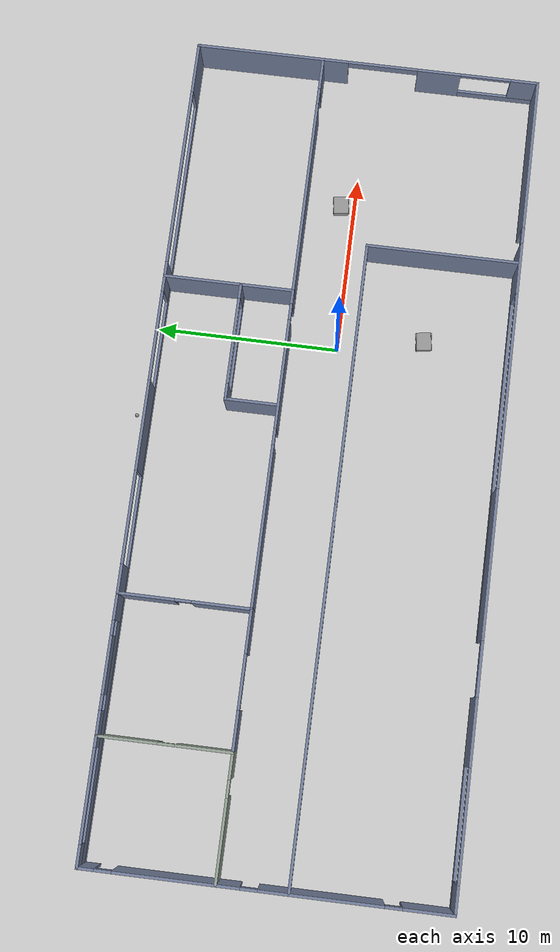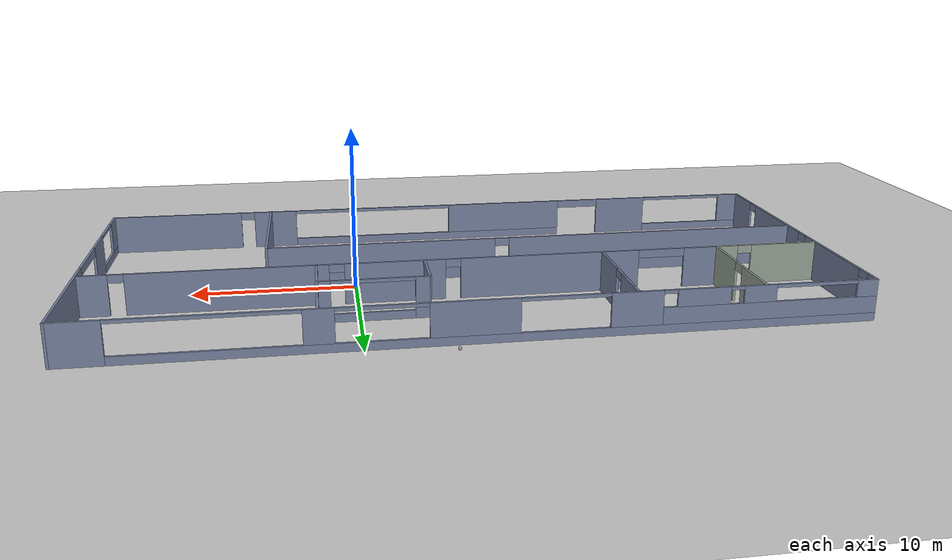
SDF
<sdf version="1.6">
 <world name="default">
  <plugin name="welcome" filename="libwelcome.so"/>
  <light name="sun" type="directional">
   <pose>0 0 10 0 -0 0</pose>
   <diffuse>0.8 0.8 0.8 1</diffuse>
   <specular>0.2 0.2 0.2 1</specular>
   <attenuation>
    <range>1000</range>
    <constant>0.9</constant>
    <linear>0.01</linear>
    <quadratic>0.001</quadratic>
   </attenuation>
   <direction>-0.5 0.1 -0.9</direction>
  </light>
  <model name="ground_plane">
   <static>1</static>
   <link name="link">
    <collision name="collision">
     <geometry><plane><normal>0 0 1</normal><size>100 100</size></plane></geometry>
     <surface><friction><ode><mu>100</mu><mu2>50</mu2></ode></friction></surface>
    </collision>
    <visual name="visual">
     <cast_shadows>0</cast_shadows>
     <geometry><plane><normal>0 0 1</normal><size>100 100</size></plane></geometry>
     <material>
      <script><uri>file://media/materials/scripts/gazebo.material</uri><name>Gazebo/Grey</name></script>
     </material>
    </visual>
   </link>
  </model>
  <gravity>0 0 -9.8</gravity>
  <magnetic_field>6e-06 2.3e-05 -4.2e-05</magnetic_field>
  <atmosphere type="adiabatic"/>
  <physics name="default_physics" default="0" type="ode">
   <max_step_size>0.001</max_step_size>
   <real_time_factor>1</real_time_factor>
   <real_time_update_rate>1000</real_time_update_rate>
  </physics>
  <scene><ambient>0.4 0.4 0.4 1</ambient><background>0.7 0.7 0.7 1</background><shadows>1</shadows></scene>
  <spherical_coordinates>
   <surface_model>EARTH_WGS84</surface_model>
   <latitude_deg>0</latitude_deg>
   <longitude_deg>0</longitude_deg>
   <elevation>0</elevation>
   <heading_deg>0</heading_deg>
  </spherical_coordinates>
  <model name="RnDBuilding">
   <pose>-6.4316 0.205557 0 0 -0 0</pose>
   <link name="Wall_0">
    <pose>22.425 0 0 0 0 -1.5708</pose>
    <visual name="Wall_0_Visual_0">
     <pose>-5.35844 0 1.25 0 -0 0</pose>
     <geometry><box><size>8.53312 0.15 2.5</size></box></geometry>
     <material>
      <script><uri>file://media/materials/scripts/gazebo.material</uri><name>Gazebo/Grey</name></script>
      <ambient>0.45098 0.498039 0.611765 1</ambient>
     </material>
     <meta><layer>0</layer></meta>
    </visual>
    <collision name="Wall_0_Collision_0">
     <geometry><box><size>8.53312 0.15 2.5</size></box></geometry>
     <pose>-5.35844 0 1.25 0 -0 0</pose>
    </collision>
    <visual name="Wall_0_Visual_1">
     <pose>4.02226 0 1.25 0 -0 0</pose>
     <geometry><box><size>2.42827 0.15 2.5</size></box></geometry>
     <material>
      <script><uri>file://media/materials/scripts/gazebo.material</uri><name>Gazebo/Grey</name></script>
      <ambient>0.45098 0.498039 0.611765 1</ambient>
     </material>
     <meta><layer>0</layer></meta>
    </visual>
    <collision name="Wall_0_Collision_1">
     <geometry><box><size>2.42827 0.15 2.5</size></box></geometry>
     <pose>4.02226 0 1.25 0 -0 0</pose>
    </collision>
    <visual name="Wall_0_Visual_2">
     <pose>7.4307 0 0.25 0 -0 0</pose>
     <geometry><box><size>4.38861 0.15 0.5</size></box></geometry>
     <material>
      <script><uri>file://media/materials/scripts/gazebo.material</uri><name>Gazebo/Grey</name></script>
      <ambient>0.45098 0.498039 0.611765 1</ambient>
     </material>
     <meta><layer>0</layer></meta>
    </visual>
    <collision name="Wall_0_Collision_2">
     <geometry><box><size>4.38861 0.15 0.5</size></box></geometry>
     <pose>7.4307 0 0.25 0 -0 0</pose>
    </collision>
    <visual name="Wall_0_Visual_3">
     <pose>8.8307 0 1.5 0 -0 0</pose>
     <geometry><box><size>1.58861 0.15 2</size></box></geometry>
     <material>
      <script><uri>file://media/materials/scripts/gazebo.material</uri><name>Gazebo/Grey</name></script>
      <ambient>0.45098 0.498039 0.611765 1</ambient>
     </material>
     <meta><layer>0</layer></meta>
    </visual>
    <collision name="Wall_0_Collision_3">
     <geometry><box><size>1.58861 0.15 2</size></box></geometry>
     <pose>8.8307 0 1.5 0 -0 0</pose>
    </collision>
    <visual name="Wall_0_Visual_4">
     <pose>0.858122 0 2.25 0 -0 0</pose>
     <geometry><box><size>3.9 0.15 0.5</size></box></geometry>
     <material>
      <script><uri>file://media/materials/scripts/gazebo.material</uri><name>Gazebo/Grey</name></script>
      <ambient>0.45098 0.498039 0.611765 1</ambient>
     </material>
     <meta><layer>0</layer></meta>
    </visual>
    <collision name="Wall_0_Collision_4">
     <geometry><box><size>3.9 0.15 0.5</size></box></geometry>
     <pose>0.858122 0 2.25 0 -0 0</pose>
    </collision>
    <visual name="Wall_0_Visual_5">
     <pose>6.63639 0 2.4 0 -0 0</pose>
     <geometry><box><size>2.8 0.15 0.2</size></box></geometry>
     <material>
      <script><uri>file://media/materials/scripts/gazebo.material</uri><name>Gazebo/Grey</name></script>
      <ambient>0.45098 0.498039 0.611765 1</ambient>
     </material>
     <meta><layer>0</layer></meta>
    </visual>
    <collision name="Wall_0_Collision_5">
     <geometry><box><size>2.8 0.15 0.2</size></box></geometry>
     <pose>6.63639 0 2.4 0 -0 0</pose>
    </collision>
   </link>
   <link name="Wall_1">
    <pose>0 -9.55 0 0 -0 3.14159</pose>
    <visual name="Wall_1_Visual_0">
     <pose>-18.1979 0 1.25 0 -0 0</pose>
     <geometry><box><size>8.60412 0.15 2.5</size></box></geometry>
     <material>
      <script><uri>file://media/materials/scripts/gazebo.material</uri><name>Gazebo/Grey</name></script>
      <ambient>0.45098 0.498039 0.611765 1</ambient>
     </material>
     <meta><layer>0</layer></meta>
    </visual>
    <collision name="Wall_1_Collision_0">
     <geometry><box><size>8.60412 0.15 2.5</size></box></geometry>
     <pose>-18.1979 0 1.25 0 -0 0</pose>
    </collision>
    <visual name="Wall_1_Visual_1">
     <pose>-11.5611 0 1.25 0 -0 0</pose>
     <geometry><box><size>2.86961 0.15 2.5</size></box></geometry>
     <material>
      <script><uri>file://media/materials/scripts/gazebo.material</uri><name>Gazebo/Grey</name></script>
      <ambient>0.45098 0.498039 0.611765 1</ambient>
     </material>
     <meta><layer>0</layer></meta>
    </visual>
    <collision name="Wall_1_Collision_1">
     <geometry><box><size>2.86961 0.15 2.5</size></box></geometry>
     <pose>-11.5611 0 1.25 0 -0 0</pose>
    </collision>
    <visual name="Wall_1_Visual_2">
     <pose>13.3816 0 1.25 0 -0 0</pose>
     <geometry><box><size>3.56837 0.15 2.5</size></box></geometry>
     <material>
      <script><uri>file://media/materials/scripts/gazebo.material</uri><name>Gazebo/Grey</name></script>
      <ambient>0.45098 0.498039 0.611765 1</ambient>
     </material>
     <meta><layer>0</layer></meta>
    </visual>
    <collision name="Wall_1_Collision_2">
     <geometry><box><size>3.56837 0.15 2.5</size></box></geometry>
     <pose>13.3816 0 1.25 0 -0 0</pose>
    </collision>
    <visual name="Wall_1_Visual_3">
     <pose>-0.714424 0 0.25 0 -0 0</pose>
     <geometry><box><size>18.8237 0.15 0.5</size></box></geometry>
     <material>
      <script><uri>file://media/materials/scripts/gazebo.material</uri><name>Gazebo/Grey</name></script>
      <ambient>0.45098 0.498039 0.611765 1</ambient>
     </material>
     <meta><layer>0</layer></meta>
    </visual>
    <collision name="Wall_1_Collision_3">
     <geometry><box><size>18.8237 0.15 0.5</size></box></geometry>
     <pose>-0.714424 0 0.25 0 -0 0</pose>
    </collision>
    <visual name="Wall_1_Visual_4">
     <pose>18.8329 0 0.25 0 -0 0</pose>
     <geometry><box><size>7.33421 0.15 0.5</size></box></geometry>
     <material>
      <script><uri>file://media/materials/scripts/gazebo.material</uri><name>Gazebo/Grey</name></script>
      <ambient>0.45098 0.498039 0.611765 1</ambient>
     </material>
     <meta><layer>0</layer></meta>
    </visual>
    <collision name="Wall_1_Collision_4">
     <geometry><box><size>7.33421 0.15 0.5</size></box></geometry>
     <pose>18.8329 0 0.25 0 -0 0</pose>
    </collision>
    <visual name="Wall_1_Visual_5">
     <pose>4.68558 0 1.5 0 -0 0</pose>
     <geometry><box><size>8.0237 0.15 2</size></box></geometry>
     <material>
      <script><uri>file://media/materials/scripts/gazebo.material</uri><name>Gazebo/Grey</name></script>
      <ambient>0.45098 0.498039 0.611765 1</ambient>
     </material>
     <meta><layer>0</layer></meta>
    </visual>
    <collision name="Wall_1_Collision_5">
     <geometry><box><size>8.0237 0.15 2</size></box></geometry>
     <pose>4.68558 0 1.5 0 -0 0</pose>
    </collision>
    <visual name="Wall_1_Visual_6">
     <pose>4.68558 0 1.5 0 -0 0</pose>
     <geometry><box><size>8.0237 0.15 2</size></box></geometry>
     <material>
      <script><uri>file://media/materials/scripts/gazebo.material</uri><name>Gazebo/Grey</name></script>
      <ambient>0.45098 0.498039 0.611765 1</ambient>
     </material>
     <meta><layer>0</layer></meta>
    </visual>
    <collision name="Wall_1_Collision_6">
     <geometry><box><size>8.0237 0.15 2</size></box></geometry>
     <pose>4.68558 0 1.5 0 -0 0</pose>
    </collision>
    <visual name="Wall_1_Visual_7">
     <pose>21.7329 0 1.5 0 -0 0</pose>
     <geometry><box><size>1.53421 0.15 2</size></box></geometry>
     <material>
      <script><uri>file://media/materials/scripts/gazebo.material</uri><name>Gazebo/Grey</name></script>
      <ambient>0.45098 0.498039 0.611765 1</ambient>
     </material>
     <meta><layer>0</layer></meta>
    </visual>
    <collision name="Wall_1_Collision_7">
     <geometry><box><size>1.53421 0.15 2</size></box></geometry>
     <pose>21.7329 0 1.5 0 -0 0</pose>
    </collision>
    <visual name="Wall_1_Visual_8">
     <pose>-13.4459 0 2.25 0 -0 0</pose>
     <geometry><box><size>0.9 0.15 0.5</size></box></geometry>
     <material>
      <script><uri>file://media/materials/scripts/gazebo.material</uri><name>Gazebo/Grey</name></script>
      <ambient>0.45098 0.498039 0.611765 1</ambient>
     </material>
     <meta><layer>0</layer></meta>
    </visual>
    <collision name="Wall_1_Collision_8">
     <geometry><box><size>0.9 0.15 0.5</size></box></geometry>
     <pose>-13.4459 0 2.25 0 -0 0</pose>
    </collision>
    <visual name="Wall_1_Visual_9">
     <pose>10.1474 0 2.25 0 -0 0</pose>
     <geometry><box><size>2.9 0.15 0.5</size></box></geometry>
     <material>
      <script><uri>file://media/materials/scripts/gazebo.material</uri><name>Gazebo/Grey</name></script>
      <ambient>0.45098 0.498039 0.611765 1</ambient>
     </material>
     <meta><layer>0</layer></meta>
    </visual>
    <collision name="Wall_1_Collision_9">
     <geometry><box><size>2.9 0.15 0.5</size></box></geometry>
     <pose>10.1474 0 2.25 0 -0 0</pose>
    </collision>
    <visual name="Wall_1_Visual_10">
     <pose>10.1474 0 2.25 0 -0 0</pose>
     <geometry><box><size>2.9 0.15 0.5</size></box></geometry>
     <material>
      <script><uri>file://media/materials/scripts/gazebo.material</uri><name>Gazebo/Grey</name></script>
      <ambient>0.45098 0.498039 0.611765 1</ambient>
     </material>
     <meta><layer>0</layer></meta>
    </visual>
    <collision name="Wall_1_Collision_10">
     <geometry><box><size>2.9 0.15 0.5</size></box></geometry>
     <pose>10.1474 0 2.25 0 -0 0</pose>
    </collision>
    <visual name="Wall_1_Visual_11">
     <pose>-4.72627 0 2.4 0 -0 0</pose>
     <geometry><box><size>10.8 0.15 0.2</size></box></geometry>
     <material>
      <script><uri>file://media/materials/scripts/gazebo.material</uri><name>Gazebo/Grey</name></script>
      <ambient>0.45098 0.498039 0.611765 1</ambient>
     </material>
     <meta><layer>0</layer></meta>
    </visual>
    <collision name="Wall_1_Collision_11">
     <geometry><box><size>10.8 0.15 0.2</size></box></geometry>
     <pose>-4.72627 0 2.4 0 -0 0</pose>
    </collision>
    <visual name="Wall_1_Visual_12">
     <pose>18.0658 0 2.4 0 -0 0</pose>
     <geometry><box><size>5.8 0.15 0.2</size></box></geometry>
     <material>
      <script><uri>file://media/materials/scripts/gazebo.material</uri><name>Gazebo/Grey</name></script>
      <ambient>0.45098 0.498039 0.611765 1</ambient>
     </material>
     <meta><layer>0</layer></meta>
    </visual>
    <collision name="Wall_1_Collision_12">
     <geometry><box><size>5.8 0.15 0.2</size></box></geometry>
     <pose>18.0658 0 2.4 0 -0 0</pose>
    </collision>
   </link>
   <link name="Wall_14">
    <collision name="Wall_14_Collision">
     <geometry><box><size>7.15 0.15 2.5</size></box></geometry>
     <pose>0 0 1.25 0 -0 0</pose>
    </collision>
    <visual name="Wall_14_Visual">
     <pose>0 0 1.25 0 -0 0</pose>
     <geometry><box><size>7.15 0.15 2.5</size></box></geometry>
     <material>
      <script><uri>file://media/materials/scripts/gazebo.material</uri><name>Gazebo/Grey</name></script>
      <ambient>0.45098 0.498039 0.611765 1</ambient>
     </material>
     <meta><layer>0</layer></meta>
    </visual>
    <pose>8.825 6.02489 0 0 -0 1.5708</pose>
   </link>
   <link name="Wall_16">
    <pose>0.15 2.52489 0 0 -0 3.14159</pose>
    <visual name="Wall_16_Visual_0">
     <pose>-8.3402 0 1.25 0 -0 0</pose>
     <geometry><box><size>0.819604 0.15 2.5</size></box></geometry>
     <material>
      <script><uri>file://media/materials/scripts/gazebo.material</uri><name>Gazebo/Grey</name></script>
      <ambient>0.45098 0.498039 0.611765 1</ambient>
     </material>
     <meta><layer>0</layer></meta>
    </visual>
    <collision name="Wall_16_Collision_0">
     <geometry><box><size>0.819604 0.15 2.5</size></box></geometry>
     <pose>-8.3402 0 1.25 0 -0 0</pose>
    </collision>
    <visual name="Wall_16_Visual_1">
     <pose>-4.01436 0 1.25 0 -0 0</pose>
     <geometry><box><size>6.03206 0.15 2.5</size></box></geometry>
     <material>
      <script><uri>file://media/materials/scripts/gazebo.material</uri><name>Gazebo/Grey</name></script>
      <ambient>0.45098 0.498039 0.611765 1</ambient>
     </material>
     <meta><layer>0</layer></meta>
    </visual>
    <collision name="Wall_16_Collision_1">
     <geometry><box><size>6.03206 0.15 2.5</size></box></geometry>
     <pose>-4.01436 0 1.25 0 -0 0</pose>
    </collision>
    <visual name="Wall_16_Visual_2">
     <pose>4.32583 0 1.25 0 -0 0</pose>
     <geometry><box><size>8.84833 0.15 2.5</size></box></geometry>
     <material>
      <script><uri>file://media/materials/scripts/gazebo.material</uri><name>Gazebo/Grey</name></script>
      <ambient>0.45098 0.498039 0.611765 1</ambient>
     </material>
     <meta><layer>0</layer></meta>
    </visual>
    <collision name="Wall_16_Collision_2">
     <geometry><box><size>8.84833 0.15 2.5</size></box></geometry>
     <pose>4.32583 0 1.25 0 -0 0</pose>
    </collision>
    <visual name="Wall_16_Visual_3">
     <pose>-7.4804 0 2.25 0 -0 0</pose>
     <geometry><box><size>0.9 0.15 0.5</size></box></geometry>
     <material>
      <script><uri>file://media/materials/scripts/gazebo.material</uri><name>Gazebo/Grey</name></script>
      <ambient>0.45098 0.498039 0.611765 1</ambient>
     </material>
     <meta><layer>0</layer></meta>
    </visual>
    <collision name="Wall_16_Collision_3">
     <geometry><box><size>0.9 0.15 0.5</size></box></geometry>
     <pose>-7.4804 0 2.25 0 -0 0</pose>
    </collision>
    <visual name="Wall_16_Visual_4">
     <pose>-0.548333 0 2.25 0 -0 0</pose>
     <geometry><box><size>0.9 0.15 0.5</size></box></geometry>
     <material>
      <script><uri>file://media/materials/scripts/gazebo.material</uri><name>Gazebo/Grey</name></script>
      <ambient>0.45098 0.498039 0.611765 1</ambient>
     </material>
     <meta><layer>0</layer></meta>
    </visual>
    <collision name="Wall_16_Collision_4">
     <geometry><box><size>0.9 0.15 0.5</size></box></geometry>
     <pose>-0.548333 0 2.25 0 -0 0</pose>
    </collision>
   </link>
   <link name="Wall_17">
    <pose>-8.525 6.02489 0 0 -0 1.5708</pose>
    <visual name="Wall_17_Visual_0">
     <pose>-1.97133 0 1.25 0 -0 0</pose>
     <geometry><box><size>3.20734 0.15 2.5</size></box></geometry>
     <material>
      <script><uri>file://media/materials/scripts/gazebo.material</uri><name>Gazebo/Grey</name></script>
      <ambient>0.45098 0.498039 0.611765 1</ambient>
     </material>
     <meta><layer>0</layer></meta>
    </visual>
    <collision name="Wall_17_Collision_0">
     <geometry><box><size>3.20734 0.15 2.5</size></box></geometry>
     <pose>-1.97133 0 1.25 0 -0 0</pose>
    </collision>
    <visual name="Wall_17_Visual_1">
     <pose>2.05367 0 1.25 0 -0 0</pose>
     <geometry><box><size>3.04266 0.15 2.5</size></box></geometry>
     <material>
      <script><uri>file://media/materials/scripts/gazebo.material</uri><name>Gazebo/Grey</name></script>
      <ambient>0.45098 0.498039 0.611765 1</ambient>
     </material>
     <meta><layer>0</layer></meta>
    </visual>
    <collision name="Wall_17_Collision_1">
     <geometry><box><size>3.04266 0.15 2.5</size></box></geometry>
     <pose>2.05367 0 1.25 0 -0 0</pose>
    </collision>
    <visual name="Wall_17_Visual_2">
     <pose>0.082341 0 2.25 0 -0 0</pose>
     <geometry><box><size>0.9 0.15 0.5</size></box></geometry>
     <material>
      <script><uri>file://media/materials/scripts/gazebo.material</uri><name>Gazebo/Grey</name></script>
      <ambient>0.45098 0.498039 0.611765 1</ambient>
     </material>
     <meta><layer>0</layer></meta>
    </visual>
    <collision name="Wall_17_Collision_2">
     <geometry><box><size>0.9 0.15 0.5</size></box></geometry>
     <pose>0.082341 0 2.25 0 -0 0</pose>
    </collision>
   </link>
   <link name="Wall_19">
    <collision name="Wall_19_Collision">
     <geometry><box><size>3 0.15 2.5</size></box></geometry>
     <pose>0 0 1.25 0 -0 0</pose>
    </collision>
    <visual name="Wall_19_Visual">
     <pose>0 0 1.25 0 -0 0</pose>
     <geometry><box><size>3 0.15 2.5</size></box></geometry>
     <material>
      <script><uri>file://media/materials/scripts/gazebo.material</uri><name>Gazebo/Grey</name></script>
      <ambient>0.45098 0.498039 0.611765 1</ambient>
     </material>
     <meta><layer>0</layer></meta>
    </visual>
    <pose>2.41972 3.94989 0 0 -0 1.5708</pose>
   </link>
   <link name="Wall_20">
    <pose>5.59472 5.37489 0 0 -0 0</pose>
    <visual name="Wall_20_Visual_0">
     <pose>-2.79096 0 1.25 0 -0 0</pose>
     <geometry><box><size>0.918074 0.15 2.5</size></box></geometry>
     <material>
      <script><uri>file://media/materials/scripts/gazebo.material</uri><name>Gazebo/Grey</name></script>
      <ambient>0.45098 0.498039 0.611765 1</ambient>
     </material>
     <meta><layer>0</layer></meta>
    </visual>
    <collision name="Wall_20_Collision_0">
     <geometry><box><size>0.918074 0.15 2.5</size></box></geometry>
     <pose>-2.79096 0 1.25 0 -0 0</pose>
    </collision>
    <visual name="Wall_20_Visual_1">
     <pose>0.459037 0 0.25 0 -0 0</pose>
     <geometry><box><size>5.58193 0.15 0.5</size></box></geometry>
     <material>
      <script><uri>file://media/materials/scripts/gazebo.material</uri><name>Gazebo/Grey</name></script>
      <ambient>0.45098 0.498039 0.611765 1</ambient>
     </material>
     <meta><layer>0</layer></meta>
    </visual>
    <collision name="Wall_20_Collision_1">
     <geometry><box><size>5.58193 0.15 0.5</size></box></geometry>
     <pose>0.459037 0 0.25 0 -0 0</pose>
    </collision>
    <visual name="Wall_20_Visual_2">
     <pose>2.85904 0 1.5 0 -0 0</pose>
     <geometry><box><size>0.781926 0.15 2</size></box></geometry>
     <material>
      <script><uri>file://media/materials/scripts/gazebo.material</uri><name>Gazebo/Grey</name></script>
      <ambient>0.45098 0.498039 0.611765 1</ambient>
     </material>
     <meta><layer>0</layer></meta>
    </visual>
    <collision name="Wall_20_Collision_2">
     <geometry><box><size>0.781926 0.15 2</size></box></geometry>
     <pose>2.85904 0 1.5 0 -0 0</pose>
    </collision>
    <visual name="Wall_20_Visual_3">
     <pose>0.068074 0 2.4 0 -0 0</pose>
     <geometry><box><size>4.8 0.15 0.2</size></box></geometry>
     <material>
      <script><uri>file://media/materials/scripts/gazebo.material</uri><name>Gazebo/Grey</name></script>
      <ambient>0.45098 0.498039 0.611765 1</ambient>
     </material>
     <meta><layer>0</layer></meta>
    </visual>
    <collision name="Wall_20_Collision_3">
     <geometry><box><size>4.8 0.15 0.2</size></box></geometry>
     <pose>0.068074 0 2.4 0 -0 0</pose>
    </collision>
   </link>
   <link name="Wall_22">
    <pose>-12.2 2.52489 0 0 -0 3.14159</pose>
    <visual name="Wall_22_Visual_0">
     <pose>-2.55908 0 1.25 0 -0 0</pose>
     <geometry><box><size>2.38184 0.15 2.5</size></box></geometry>
     <material>
      <script><uri>file://media/materials/scripts/gazebo.material</uri><name>Gazebo/Grey</name></script>
      <ambient>0.45098 0.498039 0.611765 1</ambient>
     </material>
     <meta><layer>0</layer></meta>
    </visual>
    <collision name="Wall_22_Collision_0">
     <geometry><box><size>2.38184 0.15 2.5</size></box></geometry>
     <pose>-2.55908 0 1.25 0 -0 0</pose>
    </collision>
    <visual name="Wall_22_Visual_1">
     <pose>2.64092 0 1.25 0 -0 0</pose>
     <geometry><box><size>2.21816 0.15 2.5</size></box></geometry>
     <material>
      <script><uri>file://media/materials/scripts/gazebo.material</uri><name>Gazebo/Grey</name></script>
      <ambient>0.45098 0.498039 0.611765 1</ambient>
     </material>
     <meta><layer>0</layer></meta>
    </visual>
    <collision name="Wall_22_Collision_1">
     <geometry><box><size>2.21816 0.15 2.5</size></box></geometry>
     <pose>2.64092 0 1.25 0 -0 0</pose>
    </collision>
    <visual name="Wall_22_Visual_2">
     <pose>0.081841 0 2.25 0 -0 0</pose>
     <geometry><box><size>2.9 0.15 0.5</size></box></geometry>
     <material>
      <script><uri>file://media/materials/scripts/gazebo.material</uri><name>Gazebo/Grey</name></script>
      <ambient>0.45098 0.498039 0.611765 1</ambient>
     </material>
     <meta><layer>0</layer></meta>
    </visual>
    <collision name="Wall_22_Collision_2">
     <geometry><box><size>2.9 0.15 0.5</size></box></geometry>
     <pose>0.081841 0 2.25 0 -0 0</pose>
    </collision>
   </link>
   <link name="Wall_23">
    <pose>-15.875 6.02489 0 0 -0 1.5708</pose>
    <visual name="Wall_23_Visual_0">
     <pose>-2.04112 0 1.25 0 -0 0</pose>
     <geometry><box><size>3.06777 0.15 2.5</size></box></geometry>
     <material>
      <script><uri>file://media/materials/scripts/gazebo.material</uri><name>Gazebo/Grey</name></script>
      <ambient>0.580392 0.631373 0.580392 1</ambient>
     </material>
     <meta><layer>0</layer></meta>
    </visual>
    <collision name="Wall_23_Collision_0">
     <geometry><box><size>3.06777 0.15 2.5</size></box></geometry>
     <pose>-2.04112 0 1.25 0 -0 0</pose>
    </collision>
    <visual name="Wall_23_Visual_1">
     <pose>1.98388 0 1.25 0 -0 0</pose>
     <geometry><box><size>3.18223 0.15 2.5</size></box></geometry>
     <material>
      <script><uri>file://media/materials/scripts/gazebo.material</uri><name>Gazebo/Grey</name></script>
      <ambient>0.580392 0.631373 0.580392 1</ambient>
     </material>
     <meta><layer>0</layer></meta>
    </visual>
    <collision name="Wall_23_Collision_1">
     <geometry><box><size>3.18223 0.15 2.5</size></box></geometry>
     <pose>1.98388 0 1.25 0 -0 0</pose>
    </collision>
    <visual name="Wall_23_Visual_2">
     <pose>-0.05723 0 2.25 0 -0 0</pose>
     <geometry><box><size>0.9 0.15 0.5</size></box></geometry>
     <material>
      <script><uri>file://media/materials/scripts/gazebo.material</uri><name>Gazebo/Grey</name></script>
      <ambient>0.580392 0.631373 0.580392 1</ambient>
     </material>
     <meta><layer>0</layer></meta>
    </visual>
    <collision name="Wall_23_Collision_2">
     <geometry><box><size>0.9 0.15 0.5</size></box></geometry>
     <pose>-0.05723 0 2.25 0 -0 0</pose>
    </collision>
   </link>
   <link name="Wall_25">
    <pose>-19.125 2.52489 0 0 -0 3.14159</pose>
    <visual name="Wall_25_Visual_0">
     <pose>-2.61069 0 1.25 0 -0 0</pose>
     <geometry><box><size>1.42861 0.15 2.5</size></box></geometry>
     <material>
      <script><uri>file://media/materials/scripts/gazebo.material</uri><name>Gazebo/Grey</name></script>
      <ambient>0.580392 0.631373 0.580392 1</ambient>
     </material>
     <meta><layer>0</layer></meta>
    </visual>
    <collision name="Wall_25_Collision_0">
     <geometry><box><size>1.42861 0.15 2.5</size></box></geometry>
     <pose>-2.61069 0 1.25 0 -0 0</pose>
    </collision>
    <visual name="Wall_25_Visual_1">
     <pose>1.16431 0 1.25 0 -0 0</pose>
     <geometry><box><size>4.32139 0.15 2.5</size></box></geometry>
     <material>
      <script><uri>file://media/materials/scripts/gazebo.material</uri><name>Gazebo/Grey</name></script>
      <ambient>0.580392 0.631373 0.580392 1</ambient>
     </material>
     <meta><layer>0</layer></meta>
    </visual>
    <collision name="Wall_25_Collision_1">
     <geometry><box><size>4.32139 0.15 2.5</size></box></geometry>
     <pose>1.16431 0 1.25 0 -0 0</pose>
    </collision>
    <visual name="Wall_25_Visual_2">
     <pose>-1.44639 0 2.25 0 -0 0</pose>
     <geometry><box><size>0.9 0.15 0.5</size></box></geometry>
     <material>
      <script><uri>file://media/materials/scripts/gazebo.material</uri><name>Gazebo/Grey</name></script>
      <ambient>0.580392 0.631373 0.580392 1</ambient>
     </material>
     <meta><layer>0</layer></meta>
    </visual>
    <collision name="Wall_25_Collision_2">
     <geometry><box><size>0.9 0.15 0.5</size></box></geometry>
     <pose>-1.44639 0 2.25 0 -0 0</pose>
    </collision>
   </link>
   <link name="Wall_27">
    <collision name="Wall_27_Collision">
     <geometry><box><size>8.5 0.15 2.5</size></box></geometry>
     <pose>0 0 1.25 0 -0 0</pose>
    </collision>
    <visual name="Wall_27_Visual">
     <pose>0 0 1.25 0 -0 0</pose>
     <geometry><box><size>8.5 0.15 2.5</size></box></geometry>
     <material>
      <script><uri>file://media/materials/scripts/gazebo.material</uri><name>Gazebo/Grey</name></script>
      <ambient>0.45098 0.498039 0.611765 1</ambient>
     </material>
     <meta><layer>0</layer></meta>
    </visual>
    <pose>11.8641 -5.3498 0 0 -0 1.5708</pose>
   </link>
   <link name="Wall_28">
    <pose>-5.23593 -1.1748 0 0 -0 3.14159</pose>
    <visual name="Wall_28_Visual_0">
     <pose>-9.94194 0 1.25 0 -0 0</pose>
     <geometry><box><size>14.4661 0.15 2.5</size></box></geometry>
     <material>
      <script><uri>file://media/materials/scripts/gazebo.material</uri><name>Gazebo/Grey</name></script>
      <ambient>0.45098 0.498039 0.611765 1</ambient>
     </material>
     <meta><layer>0</layer></meta>
    </visual>
    <collision name="Wall_28_Collision_0">
     <geometry><box><size>14.4661 0.15 2.5</size></box></geometry>
     <pose>-9.94194 0 1.25 0 -0 0</pose>
    </collision>
    <visual name="Wall_28_Visual_1">
     <pose>7.68306 0 1.25 0 -0 0</pose>
     <geometry><box><size>18.9839 0.15 2.5</size></box></geometry>
     <material>
      <script><uri>file://media/materials/scripts/gazebo.material</uri><name>Gazebo/Grey</name></script>
      <ambient>0.45098 0.498039 0.611765 1</ambient>
     </material>
     <meta><layer>0</layer></meta>
    </visual>
    <collision name="Wall_28_Collision_1">
     <geometry><box><size>18.9839 0.15 2.5</size></box></geometry>
     <pose>7.68306 0 1.25 0 -0 0</pose>
    </collision>
    <visual name="Wall_28_Visual_2">
     <pose>-2.25887 0 2.25 0 -0 0</pose>
     <geometry><box><size>0.9 0.15 0.5</size></box></geometry>
     <material>
      <script><uri>file://media/materials/scripts/gazebo.material</uri><name>Gazebo/Grey</name></script>
      <ambient>0.45098 0.498039 0.611765 1</ambient>
     </material>
     <meta><layer>0</layer></meta>
    </visual>
    <collision name="Wall_28_Collision_2">
     <geometry><box><size>0.9 0.15 0.5</size></box></geometry>
     <pose>-2.25887 0 2.25 0 -0 0</pose>
    </collision>
   </link>
   <link name="Wall_5">
    <pose>0 9.55 0 0 -0 3.14159</pose>
    <visual name="Wall_5_Visual_0">
     <pose>-21.0608 0 1.25 0 -0 0</pose>
     <geometry><box><size>2.87831 0.15 2.5</size></box></geometry>
     <material>
      <script><uri>file://media/materials/scripts/gazebo.material</uri><name>Gazebo/Grey</name></script>
      <ambient>0.45098 0.498039 0.611765 1</ambient>
     </material>
     <meta><layer>0</layer></meta>
    </visual>
    <collision name="Wall_5_Collision_0">
     <geometry><box><size>2.87831 0.15 2.5</size></box></geometry>
     <pose>-21.0608 0 1.25 0 -0 0</pose>
    </collision>
    <visual name="Wall_5_Visual_1">
     <pose>1.43915 0 0.25 0 -0 0</pose>
     <geometry><box><size>42.1217 0.15 0.5</size></box></geometry>
     <material>
      <script><uri>file://media/materials/scripts/gazebo.material</uri><name>Gazebo/Grey</name></script>
      <ambient>0.45098 0.498039 0.611765 1</ambient>
     </material>
     <meta><layer>0</layer></meta>
    </visual>
    <collision name="Wall_5_Collision_1">
     <geometry><box><size>42.1217 0.15 0.5</size></box></geometry>
     <pose>1.43915 0 0.25 0 -0 0</pose>
    </collision>
    <visual name="Wall_5_Visual_2">
     <pose>-8.78055 0 1.5 0 -0 0</pose>
     <geometry><box><size>1.68228 0.15 2</size></box></geometry>
     <material>
      <script><uri>file://media/materials/scripts/gazebo.material</uri><name>Gazebo/Grey</name></script>
      <ambient>0.45098 0.498039 0.611765 1</ambient>
     </material>
     <meta><layer>0</layer></meta>
    </visual>
    <collision name="Wall_5_Collision_2">
     <geometry><box><size>1.68228 0.15 2</size></box></geometry>
     <pose>-8.78055 0 1.5 0 -0 0</pose>
    </collision>
    <visual name="Wall_5_Visual_3">
     <pose>-0.470461 0 1.5 0 -0 0</pose>
     <geometry><box><size>4.93789 0.15 2</size></box></geometry>
     <material>
      <script><uri>file://media/materials/scripts/gazebo.material</uri><name>Gazebo/Grey</name></script>
      <ambient>0.45098 0.498039 0.611765 1</ambient>
     </material>
     <meta><layer>0</layer></meta>
    </visual>
    <collision name="Wall_5_Collision_3">
     <geometry><box><size>4.93789 0.15 2</size></box></geometry>
     <pose>-0.470461 0 1.5 0 -0 0</pose>
    </collision>
    <visual name="Wall_5_Visual_4">
     <pose>8.4703 0 1.5 0 -0 0</pose>
     <geometry><box><size>2.94362 0.15 2</size></box></geometry>
     <material>
      <script><uri>file://media/materials/scripts/gazebo.material</uri><name>Gazebo/Grey</name></script>
      <ambient>0.45098 0.498039 0.611765 1</ambient>
     </material>
     <meta><layer>0</layer></meta>
    </visual>
    <collision name="Wall_5_Collision_4">
     <geometry><box><size>2.94362 0.15 2</size></box></geometry>
     <pose>8.4703 0 1.5 0 -0 0</pose>
    </collision>
    <visual name="Wall_5_Visual_5">
     <pose>16.2211 0 1 0 -0 0</pose>
     <geometry><box><size>12.5579 0.15 1</size></box></geometry>
     <material>
      <script><uri>file://media/materials/scripts/gazebo.material</uri><name>Gazebo/Grey</name></script>
      <ambient>0.45098 0.498039 0.611765 1</ambient>
     </material>
     <meta><layer>0</layer></meta>
    </visual>
    <collision name="Wall_5_Collision_5">
     <geometry><box><size>12.5579 0.15 1</size></box></geometry>
     <pose>16.2211 0 1 0 -0 0</pose>
    </collision>
    <visual name="Wall_5_Visual_6">
     <pose>12.2637 0 2 0 -0 0</pose>
     <geometry><box><size>3.04328 0.15 1</size></box></geometry>
     <material>
      <script><uri>file://media/materials/scripts/gazebo.material</uri><name>Gazebo/Grey</name></script>
      <ambient>0.45098 0.498039 0.611765 1</ambient>
     </material>
     <meta><layer>0</layer></meta>
    </visual>
    <collision name="Wall_5_Collision_6">
     <geometry><box><size>3.04328 0.15 1</size></box></geometry>
     <pose>12.2637 0 2 0 -0 0</pose>
    </collision>
    <visual name="Wall_5_Visual_7">
     <pose>15.5269 0 2 0 -0 0</pose>
     <geometry><box><size>1.88294 0.15 1</size></box></geometry>
     <material>
      <script><uri>file://media/materials/scripts/gazebo.material</uri><name>Gazebo/Grey</name></script>
      <ambient>0.45098 0.498039 0.611765 1</ambient>
     </material>
     <meta><layer>0</layer></meta>
    </visual>
    <collision name="Wall_5_Collision_7">
     <geometry><box><size>1.88294 0.15 1</size></box></geometry>
     <pose>15.5269 0 2 0 -0 0</pose>
    </collision>
    <visual name="Wall_5_Visual_8">
     <pose>21.8842 0 2 0 -0 0</pose>
     <geometry><box><size>1.23167 0.15 1</size></box></geometry>
     <material>
      <script><uri>file://media/materials/scripts/gazebo.material</uri><name>Gazebo/Grey</name></script>
      <ambient>0.45098 0.498039 0.611765 1</ambient>
     </material>
     <meta><layer>0</layer></meta>
    </visual>
    <collision name="Wall_5_Collision_8">
     <geometry><box><size>1.23167 0.15 1</size></box></geometry>
     <pose>21.8842 0 2 0 -0 0</pose>
    </collision>
    <visual name="Wall_5_Visual_9">
     <pose>-14.6217 0 2.4 0 -0 0</pose>
     <geometry><box><size>10 0.15 0.2</size></box></geometry>
     <material>
      <script><uri>file://media/materials/scripts/gazebo.material</uri><name>Gazebo/Grey</name></script>
      <ambient>0.45098 0.498039 0.611765 1</ambient>
     </material>
     <meta><layer>0</layer></meta>
    </visual>
    <collision name="Wall_5_Collision_9">
     <geometry><box><size>10 0.15 0.2</size></box></geometry>
     <pose>-14.6217 0 2.4 0 -0 0</pose>
    </collision>
    <visual name="Wall_5_Visual_10">
     <pose>-5.43941 0 2.4 0 -0 0</pose>
     <geometry><box><size>5 0.15 0.2</size></box></geometry>
     <material>
      <script><uri>file://media/materials/scripts/gazebo.material</uri><name>Gazebo/Grey</name></script>
      <ambient>0.45098 0.498039 0.611765 1</ambient>
     </material>
     <meta><layer>0</layer></meta>
    </visual>
    <collision name="Wall_5_Collision_10">
     <geometry><box><size>5 0.15 0.2</size></box></geometry>
     <pose>-5.43941 0 2.4 0 -0 0</pose>
    </collision>
    <visual name="Wall_5_Visual_11">
     <pose>4.49848 0 2.4 0 -0 0</pose>
     <geometry><box><size>5 0.15 0.2</size></box></geometry>
     <material>
      <script><uri>file://media/materials/scripts/gazebo.material</uri><name>Gazebo/Grey</name></script>
      <ambient>0.45098 0.498039 0.611765 1</ambient>
     </material>
     <meta><layer>0</layer></meta>
    </visual>
    <collision name="Wall_5_Collision_11">
     <geometry><box><size>5 0.15 0.2</size></box></geometry>
     <pose>4.49848 0 2.4 0 -0 0</pose>
    </collision>
    <visual name="Wall_5_Visual_12">
     <pose>10.3421 0 2.4 0 -0 0</pose>
     <geometry><box><size>0.8 0.15 0.2</size></box></geometry>
     <material>
      <script><uri>file://media/materials/scripts/gazebo.material</uri><name>Gazebo/Grey</name></script>
      <ambient>0.45098 0.498039 0.611765 1</ambient>
     </material>
     <meta><layer>0</layer></meta>
    </visual>
    <collision name="Wall_5_Collision_12">
     <geometry><box><size>0.8 0.15 0.2</size></box></geometry>
     <pose>10.3421 0 2.4 0 -0 0</pose>
    </collision>
    <visual name="Wall_5_Visual_13">
     <pose>14.1854 0 2.4 0 -0 0</pose>
     <geometry><box><size>0.8 0.15 0.2</size></box></geometry>
     <material>
      <script><uri>file://media/materials/scripts/gazebo.material</uri><name>Gazebo/Grey</name></script>
      <ambient>0.45098 0.498039 0.611765 1</ambient>
     </material>
     <meta><layer>0</layer></meta>
    </visual>
    <collision name="Wall_5_Collision_13">
     <geometry><box><size>0.8 0.15 0.2</size></box></geometry>
     <pose>14.1854 0 2.4 0 -0 0</pose>
    </collision>
    <visual name="Wall_5_Visual_14">
     <pose>18.8683 0 2.4 0 -0 0</pose>
     <geometry><box><size>4.8 0.15 0.2</size></box></geometry>
     <material>
      <script><uri>file://media/materials/scripts/gazebo.material</uri><name>Gazebo/Grey</name></script>
      <ambient>0.45098 0.498039 0.611765 1</ambient>
     </material>
     <meta><layer>0</layer></meta>
    </visual>
    <collision name="Wall_5_Collision_14">
     <geometry><box><size>4.8 0.15 0.2</size></box></geometry>
     <pose>18.8683 0 2.4 0 -0 0</pose>
    </collision>
   </link>
   <link name="Wall_6">
    <pose>-22.425 0 0 0 0 -1.5708</pose>
    <visual name="Wall_6_Visual_0">
     <pose>-9.16117 0 1.25 0 -0 0</pose>
     <geometry><box><size>0.92767 0.15 2.5</size></box></geometry>
     <material>
      <script><uri>file://media/materials/scripts/gazebo.material</uri><name>Gazebo/Grey</name></script>
      <ambient>0.45098 0.498039 0.611765 1</ambient>
     </material>
     <meta><layer>0</layer></meta>
    </visual>
    <collision name="Wall_6_Collision_0">
     <geometry><box><size>0.92767 0.15 2.5</size></box></geometry>
     <pose>-9.16117 0 1.25 0 -0 0</pose>
    </collision>
    <visual name="Wall_6_Visual_1">
     <pose>-4.54868 0 1.25 0 -0 0</pose>
     <geometry><box><size>6.4973 0.15 2.5</size></box></geometry>
     <material>
      <script><uri>file://media/materials/scripts/gazebo.material</uri><name>Gazebo/Grey</name></script>
      <ambient>0.45098 0.498039 0.611765 1</ambient>
     </material>
     <meta><layer>0</layer></meta>
    </visual>
    <collision name="Wall_6_Collision_1">
     <geometry><box><size>6.4973 0.15 2.5</size></box></geometry>
     <pose>-4.54868 0 1.25 0 -0 0</pose>
    </collision>
    <visual name="Wall_6_Visual_2">
     <pose>2.8021 0 1.25 0 -0 0</pose>
     <geometry><box><size>6.40425 0.15 2.5</size></box></geometry>
     <material>
      <script><uri>file://media/materials/scripts/gazebo.material</uri><name>Gazebo/Grey</name></script>
      <ambient>0.45098 0.498039 0.611765 1</ambient>
     </material>
     <meta><layer>0</layer></meta>
    </visual>
    <collision name="Wall_6_Collision_2">
     <geometry><box><size>6.40425 0.15 2.5</size></box></geometry>
     <pose>2.8021 0 1.25 0 -0 0</pose>
    </collision>
    <visual name="Wall_6_Visual_3">
     <pose>8.26461 0 1.25 0 -0 0</pose>
     <geometry><box><size>2.72077 0.15 2.5</size></box></geometry>
     <material>
      <script><uri>file://media/materials/scripts/gazebo.material</uri><name>Gazebo/Grey</name></script>
      <ambient>0.45098 0.498039 0.611765 1</ambient>
     </material>
     <meta><layer>0</layer></meta>
    </visual>
    <collision name="Wall_6_Collision_3">
     <geometry><box><size>2.72077 0.15 2.5</size></box></geometry>
     <pose>8.26461 0 1.25 0 -0 0</pose>
    </collision>
    <visual name="Wall_6_Visual_4">
     <pose>-8.24733 0 2.25 0 -0 0</pose>
     <geometry><box><size>0.9 0.15 0.5</size></box></geometry>
     <material>
      <script><uri>file://media/materials/scripts/gazebo.material</uri><name>Gazebo/Grey</name></script>
      <ambient>0.45098 0.498039 0.611765 1</ambient>
     </material>
     <meta><layer>0</layer></meta>
    </visual>
    <collision name="Wall_6_Collision_4">
     <geometry><box><size>0.9 0.15 0.5</size></box></geometry>
     <pose>-8.24733 0 2.25 0 -0 0</pose>
    </collision>
    <visual name="Wall_6_Visual_5">
     <pose>-0.850028 0 2.25 0 -0 0</pose>
     <geometry><box><size>0.9 0.15 0.5</size></box></geometry>
     <material>
      <script><uri>file://media/materials/scripts/gazebo.material</uri><name>Gazebo/Grey</name></script>
      <ambient>0.45098 0.498039 0.611765 1</ambient>
     </material>
     <meta><layer>0</layer></meta>
    </visual>
    <collision name="Wall_6_Collision_5">
     <geometry><box><size>0.9 0.15 0.5</size></box></geometry>
     <pose>-0.850028 0 2.25 0 -0 0</pose>
    </collision>
    <visual name="Wall_6_Visual_6">
     <pose>6.45423 0 2.25 0 -0 0</pose>
     <geometry><box><size>0.9 0.15 0.5</size></box></geometry>
     <material>
      <script><uri>file://media/materials/scripts/gazebo.material</uri><name>Gazebo/Grey</name></script>
      <ambient>0.45098 0.498039 0.611765 1</ambient>
     </material>
     <meta><layer>0</layer></meta>
    </visual>
    <collision name="Wall_6_Collision_6">
     <geometry><box><size>0.9 0.15 0.5</size></box></geometry>
     <pose>6.45423 0 2.25 0 -0 0</pose>
    </collision>
   </link>
   <link name="Wall_9">
    <pose>15.625 2.52489 0 0 -0 3.14159</pose>
    <visual name="Wall_9_Visual_0">
     <pose>-5.94593 0 1.25 0 -0 0</pose>
     <geometry><box><size>1.85815 0.15 2.5</size></box></geometry>
     <material>
      <script><uri>file://media/materials/scripts/gazebo.material</uri><name>Gazebo/Grey</name></script>
      <ambient>0.45098 0.498039 0.611765 1</ambient>
     </material>
     <meta><layer>0</layer></meta>
    </visual>
    <collision name="Wall_9_Collision_0">
     <geometry><box><size>1.85815 0.15 2.5</size></box></geometry>
     <pose>-5.94593 0 1.25 0 -0 0</pose>
    </collision>
    <visual name="Wall_9_Visual_1">
     <pose>1.37907 0 1.25 0 -0 0</pose>
     <geometry><box><size>10.9919 0.15 2.5</size></box></geometry>
     <material>
      <script><uri>file://media/materials/scripts/gazebo.material</uri><name>Gazebo/Grey</name></script>
      <ambient>0.45098 0.498039 0.611765 1</ambient>
     </material>
     <meta><layer>0</layer></meta>
    </visual>
    <collision name="Wall_9_Collision_1">
     <geometry><box><size>10.9919 0.15 2.5</size></box></geometry>
     <pose>1.37907 0 1.25 0 -0 0</pose>
    </collision>
    <visual name="Wall_9_Visual_2">
     <pose>-4.56685 0 2.25 0 -0 0</pose>
     <geometry><box><size>0.9 0.15 0.5</size></box></geometry>
     <material>
      <script><uri>file://media/materials/scripts/gazebo.material</uri><name>Gazebo/Grey</name></script>
      <ambient>0.45098 0.498039 0.611765 1</ambient>
     </material>
     <meta><layer>0</layer></meta>
    </visual>
    <collision name="Wall_9_Collision_2">
     <geometry><box><size>0.9 0.15 0.5</size></box></geometry>
     <pose>-4.56685 0 2.25 0 -0 0</pose>
    </collision>
   </link>
   <static>1</static>
  </model>
  <model name="Robot_4WD_0">
   <link name="link_0">
    <inertial>
     <mass>1</mass>
     <inertia>
      <ixx>0.166667</ixx>
      <ixy>0</ixy>
      <ixz>0</ixz>
      <iyy>0.166667</iyy>
      <iyz>0</iyz>
      <izz>0.166667</izz>
     </inertia>
    </inertial>
    <visual name="visual">
     <geometry><box><size>1 0.8 0.3</size></box></geometry>
     <material>
      <lighting>1</lighting>
      <script><uri>file://media/materials/scripts/gazebo.material</uri><name>Gazebo/Grey</name></script>
      <shader type="pixel"><normal_map>__default__</normal_map></shader>
      <ambient>0.3 0.3 0.3 1</ambient>
      <diffuse>0.7 0.7 0.7 1</diffuse>
      <specular>0.01 0.01 0.01 1</specular>
      <emissive>0 0 0 1</emissive>
     </material>
    </visual>
    <collision name="collision">
     <geometry><box><size>1 0.8 0.3</size></box></geometry>
     <surface>
      <friction>
       <ode><mu>1</mu><mu2>1</mu2><fdir1>0 0 0</fdir1><slip1>0</slip1><slip2>0</slip2></ode>
       <torsional>
        <coefficient>1</coefficient>
        <patch_radius>0</patch_radius>
        <surface_radius>0</surface_radius>
        <use_patch_radius>1</use_patch_radius>
        <ode><slip>0</slip></ode>
       </torsional>
      </friction>
      <bounce><restitution_coefficient>0</restitution_coefficient><threshold>1e+06</threshold></bounce>
      <contact>
       <collide_without_contact>0</collide_without_contact>
       <collide_without_contact_bitmask>1</collide_without_contact_bitmask>
       <collide_bitmask>1</collide_bitmask>
       <ode>
        <soft_cfm>0</soft_cfm>
        <soft_erp>0.2</soft_erp>
        <kp>1e+13</kp>
        <kd>1</kd>
        <max_vel>0.01</max_vel>
        <min_depth>0</min_depth>
       </ode>
       <bullet>
        <split_impulse>1</split_impulse>
        <split_impulse_penetration_threshold>-0.01</split_impulse_penetration_threshold>
        <soft_cfm>0</soft_cfm>
        <soft_erp>0.2</soft_erp>
        <kp>1e+13</kp>
        <kd>1</kd>
       </bullet>
      </contact>
     </surface>
    </collision>
   </link>
   <link name="link_1">
    <pose>-0.3 -0.425001 0 1.5708 -0 0</pose>
    <inertial>
     <mass>1</mass>
     <inertia><ixx>0.145833</ixx><ixy>0</ixy><ixz>0</ixz><iyy>0.145833</iyy><iyz>0</iyz><izz>0.125</izz></inertia>
    </inertial>
    <visual name="visual">
     <geometry><cylinder><radius>0.2</radius><length>0.05</length></cylinder></geometry>
     <material>
      <lighting>1</lighting>
      <script><uri>file://media/materials/scripts/gazebo.material</uri><name>Gazebo/Grey</name></script>
      <shader type="pixel"><normal_map>__default__</normal_map></shader>
      <ambient>0.3 0.3 0.3 1</ambient>
      <diffuse>0.7 0.7 0.7 1</diffuse>
      <specular>0.01 0.01 0.01 1</specular>
      <emissive>0 0 0 1</emissive>
     </material>
    </visual>
    <collision name="collision">
     <geometry><cylinder><radius>0.2</radius><length>0.05</length></cylinder></geometry>
     <surface>
      <friction>
       <ode><mu>1</mu><mu2>1</mu2><fdir1>0 0 0</fdir1><slip1>0</slip1><slip2>0</slip2></ode>
       <torsional>
        <coefficient>1</coefficient>
        <patch_radius>0</patch_radius>
        <surface_radius>0</surface_radius>
        <use_patch_radius>1</use_patch_radius>
        <ode><slip>0</slip></ode>
       </torsional>
      </friction>
      <bounce><restitution_coefficient>0</restitution_coefficient><threshold>1e+06</threshold></bounce>
      <contact>
       <collide_without_contact>0</collide_without_contact>
       <collide_without_contact_bitmask>1</collide_without_contact_bitmask>
       <collide_bitmask>1</collide_bitmask>
       <ode>
        <soft_cfm>0</soft_cfm>
        <soft_erp>0.2</soft_erp>
        <kp>1e+13</kp>
        <kd>1</kd>
        <max_vel>0.01</max_vel>
        <min_depth>0</min_depth>
       </ode>
       <bullet>
        <split_impulse>1</split_impulse>
        <split_impulse_penetration_threshold>-0.01</split_impulse_penetration_threshold>
        <soft_cfm>0</soft_cfm>
        <soft_erp>0.2</soft_erp>
        <kp>1e+13</kp>
        <kd>1</kd>
       </bullet>
      </contact>
     </surface>
    </collision>
   </link>
   <link name="link_1_clone">
    <pose>0.3 0.425001 0 1.5708 -0 0</pose>
    <inertial>
     <mass>1</mass>
     <inertia><ixx>0.145833</ixx><ixy>0</ixy><ixz>0</ixz><iyy>0.145833</iyy><iyz>0</iyz><izz>0.125</izz></inertia>
    </inertial>
    <visual name="visual">
     <geometry><cylinder><radius>0.2</radius><length>0.05</length></cylinder></geometry>
     <material>
      <lighting>1</lighting>
      <script><uri>file://media/materials/scripts/gazebo.material</uri><name>Gazebo/Grey</name></script>
      <shader type="pixel"><normal_map>__default__</normal_map></shader>
      <ambient>0.3 0.3 0.3 1</ambient>
      <diffuse>0.7 0.7 0.7 1</diffuse>
      <specular>0.01 0.01 0.01 1</specular>
      <emissive>0 0 0 1</emissive>
     </material>
    </visual>
    <collision name="collision">
     <geometry><cylinder><radius>0.2</radius><length>0.05</length></cylinder></geometry>
     <surface>
      <friction>
       <ode><mu>1</mu><mu2>1</mu2><fdir1>0 0 0</fdir1><slip1>0</slip1><slip2>0</slip2></ode>
       <torsional>
        <coefficient>1</coefficient>
        <patch_radius>0</patch_radius>
        <surface_radius>0</surface_radius>
        <use_patch_radius>1</use_patch_radius>
        <ode><slip>0</slip></ode>
       </torsional>
      </friction>
      <bounce><restitution_coefficient>0</restitution_coefficient><threshold>1e+06</threshold></bounce>
      <contact>
       <collide_without_contact>0</collide_without_contact>
       <collide_without_contact_bitmask>1</collide_without_contact_bitmask>
       <collide_bitmask>1</collide_bitmask>
       <ode>
        <soft_cfm>0</soft_cfm>
        <soft_erp>0.2</soft_erp>
        <kp>1e+13</kp>
        <kd>1</kd>
        <max_vel>0.01</max_vel>
        <min_depth>0</min_depth>
       </ode>
       <bullet>
        <split_impulse>1</split_impulse>
        <split_impulse_penetration_threshold>-0.01</split_impulse_penetration_threshold>
        <soft_cfm>0</soft_cfm>
        <soft_erp>0.2</soft_erp>
        <kp>1e+13</kp>
        <kd>1</kd>
       </bullet>
      </contact>
     </surface>
    </collision>
   </link>
   <link name="link_1_clone_0">
    <pose>-0.3 0.425001 0 1.5708 -0 0</pose>
    <inertial>
     <mass>1</mass>
     <inertia><ixx>0.145833</ixx><ixy>0</ixy><ixz>0</ixz><iyy>0.145833</iyy><iyz>0</iyz><izz>0.125</izz></inertia>
    </inertial>
    <visual name="visual">
     <geometry><cylinder><radius>0.2</radius><length>0.05</length></cylinder></geometry>
     <material>
      <lighting>1</lighting>
      <script><uri>file://media/materials/scripts/gazebo.material</uri><name>Gazebo/Grey</name></script>
      <shader type="pixel"><normal_map>__default__</normal_map></shader>
      <ambient>0.3 0.3 0.3 1</ambient>
      <diffuse>0.7 0.7 0.7 1</diffuse>
      <specular>0.01 0.01 0.01 1</specular>
      <emissive>0 0 0 1</emissive>
     </material>
    </visual>
    <collision name="collision">
     <geometry><cylinder><radius>0.2</radius><length>0.05</length></cylinder></geometry>
     <surface>
      <friction>
       <ode><mu>1</mu><mu2>1</mu2><fdir1>0 0 0</fdir1><slip1>0</slip1><slip2>0</slip2></ode>
       <torsional>
        <coefficient>1</coefficient>
        <patch_radius>0</patch_radius>
        <surface_radius>0</surface_radius>
        <use_patch_radius>1</use_patch_radius>
        <ode><slip>0</slip></ode>
       </torsional>
      </friction>
      <bounce><restitution_coefficient>0</restitution_coefficient><threshold>1e+06</threshold></bounce>
      <contact>
       <collide_without_contact>0</collide_without_contact>
       <collide_without_contact_bitmask>1</collide_without_contact_bitmask>
       <collide_bitmask>1</collide_bitmask>
       <ode>
        <soft_cfm>0</soft_cfm>
        <soft_erp>0.2</soft_erp>
        <kp>1e+13</kp>
        <kd>1</kd>
        <max_vel>0.01</max_vel>
        <min_depth>0</min_depth>
       </ode>
       <bullet>
        <split_impulse>1</split_impulse>
        <split_impulse_penetration_threshold>-0.01</split_impulse_penetration_threshold>
        <soft_cfm>0</soft_cfm>
        <soft_erp>0.2</soft_erp>
        <kp>1e+13</kp>
        <kd>1</kd>
       </bullet>
      </contact>
     </surface>
    </collision>
   </link>
   <link name="link_1_clone_1">
    <pose>0.3 -0.425001 0 1.5708 -0 0</pose>
    <inertial>
     <mass>1</mass>
     <inertia><ixx>0.145833</ixx><ixy>0</ixy><ixz>0</ixz><iyy>0.145833</iyy><iyz>0</iyz><izz>0.125</izz></inertia>
    </inertial>
    <visual name="visual">
     <geometry><cylinder><radius>0.2</radius><length>0.05</length></cylinder></geometry>
     <material>
      <lighting>1</lighting>
      <script><uri>file://media/materials/scripts/gazebo.material</uri><name>Gazebo/Grey</name></script>
      <shader type="pixel"><normal_map>__default__</normal_map></shader>
      <ambient>0.3 0.3 0.3 1</ambient>
      <diffuse>0.7 0.7 0.7 1</diffuse>
      <specular>0.01 0.01 0.01 1</specular>
      <emissive>0 0 0 1</emissive>
     </material>
    </visual>
    <collision name="collision">
     <geometry><cylinder><radius>0.2</radius><length>0.05</length></cylinder></geometry>
     <surface>
      <friction>
       <ode><mu>1</mu><mu2>1</mu2><fdir1>0 0 0</fdir1><slip1>0</slip1><slip2>0</slip2></ode>
       <torsional>
        <coefficient>1</coefficient>
        <patch_radius>0</patch_radius>
        <surface_radius>0</surface_radius>
        <use_patch_radius>1</use_patch_radius>
        <ode><slip>0</slip></ode>
       </torsional>
      </friction>
      <bounce><restitution_coefficient>0</restitution_coefficient><threshold>1e+06</threshold></bounce>
      <contact>
       <collide_without_contact>0</collide_without_contact>
       <collide_without_contact_bitmask>1</collide_without_contact_bitmask>
       <collide_bitmask>1</collide_bitmask>
       <ode>
        <soft_cfm>0</soft_cfm>
        <soft_erp>0.2</soft_erp>
        <kp>1e+13</kp>
        <kd>1</kd>
        <max_vel>0.01</max_vel>
        <min_depth>0</min_depth>
       </ode>
       <bullet>
        <split_impulse>1</split_impulse>
        <split_impulse_penetration_threshold>-0.01</split_impulse_penetration_threshold>
        <soft_cfm>0</soft_cfm>
        <soft_erp>0.2</soft_erp>
        <kp>1e+13</kp>
        <kd>1</kd>
       </bullet>
      </contact>
     </surface>
    </collision>
   </link>
   <joint name="link_0_JOINT_0" type="revolute">
    <parent>link_0</parent>
    <child>link_1_clone_1</child>
    <axis>
     <xyz>1 0 -0.2</xyz>
     <use_parent_model_frame>0</use_parent_model_frame>
     <limit>
      <lower>-1.79769e+308</lower>
      <upper>1.79769e+308</upper>
      <effort>-1</effort>
      <velocity>-1</velocity>
     </limit>
     <dynamics>
      <spring_reference>0</spring_reference>
      <spring_stiffness>0</spring_stiffness>
      <damping>0</damping>
     </dynamics>
    </axis>
    <physics>
     <ode><limit><cfm>0</cfm><erp>0.2</erp></limit><suspension><cfm>0</cfm><erp>0.2</erp></suspension></ode>
    </physics>
   </joint>
   <joint name="link_0_JOINT_1" type="revolute">
    <parent>link_0</parent>
    <child>link_1</child>
    <axis>
     <xyz>1 0 0</xyz>
     <use_parent_model_frame>0</use_parent_model_frame>
     <limit>
      <lower>-1.79769e+308</lower>
      <upper>1.79769e+308</upper>
      <effort>-1</effort>
      <velocity>-1</velocity>
     </limit>
     <dynamics>
      <spring_reference>0</spring_reference>
      <spring_stiffness>0</spring_stiffness>
      <damping>0</damping>
     </dynamics>
    </axis>
    <physics>
     <ode><limit><cfm>0</cfm><erp>0.2</erp></limit><suspension><cfm>0</cfm><erp>0.2</erp></suspension></ode>
    </physics>
   </joint>
   <joint name="link_0_JOINT_2" type="revolute">
    <parent>link_0</parent>
    <child>link_1_clone</child>
    <axis>
     <xyz>1 0 0</xyz>
     <use_parent_model_frame>0</use_parent_model_frame>
     <limit>
      <lower>-1.79769e+308</lower>
      <upper>1.79769e+308</upper>
      <effort>-1</effort>
      <velocity>-1</velocity>
     </limit>
     <dynamics>
      <spring_reference>0</spring_reference>
      <spring_stiffness>0</spring_stiffness>
      <damping>0</damping>
     </dynamics>
    </axis>
    <physics>
     <ode><limit><cfm>0</cfm><erp>0.2</erp></limit><suspension><cfm>0</cfm><erp>0.2</erp></suspension></ode>
    </physics>
   </joint>
   <joint name="link_0_JOINT_3" type="revolute">
    <parent>link_0</parent>
    <child>link_1_clone_0</child>
    <axis>
     <xyz>1 0 0</xyz>
     <use_parent_model_frame>0</use_parent_model_frame>
     <limit>
      <lower>-1.79769e+308</lower>
      <upper>1.79769e+308</upper>
      <effort>-1</effort>
      <velocity>-1</velocity>
     </limit>
     <dynamics>
      <spring_reference>0</spring_reference>
      <spring_stiffness>0</spring_stiffness>
      <damping>0</damping>
     </dynamics>
    </axis>
    <physics>
     <ode><limit><cfm>0</cfm><erp>0.2</erp></limit><suspension><cfm>0</cfm><erp>0.2</erp></suspension></ode>
    </physics>
   </joint>
   <static>0</static>
   <pose>1.01844 -4.70837 0.2 0 -0 0.126058</pose>
  </model>
  <model name="Robot_4WD_1">
   <link name="link_0">
    <inertial>
     <mass>1</mass>
     <inertia>
      <ixx>0.166667</ixx>
      <ixy>0</ixy>
      <ixz>0</ixz>
      <iyy>0.166667</iyy>
      <iyz>0</iyz>
      <izz>0.166667</izz>
     </inertia>
    </inertial>
    <visual name="visual">
     <geometry><box><size>1 0.8 0.3</size></box></geometry>
     <material>
      <lighting>1</lighting>
      <script><uri>file://media/materials/scripts/gazebo.material</uri><name>Gazebo/Grey</name></script>
      <shader type="pixel"><normal_map>__default__</normal_map></shader>
      <ambient>0.3 0.3 0.3 1</ambient>
      <diffuse>0.7 0.7 0.7 1</diffuse>
      <specular>0.01 0.01 0.01 1</specular>
      <emissive>0 0 0 1</emissive>
     </material>
    </visual>
    <collision name="collision">
     <geometry><box><size>1 0.8 0.3</size></box></geometry>
     <surface>
      <friction>
       <ode><mu>1</mu><mu2>1</mu2><fdir1>0 0 0</fdir1><slip1>0</slip1><slip2>0</slip2></ode>
       <torsional>
        <coefficient>1</coefficient>
        <patch_radius>0</patch_radius>
        <surface_radius>0</surface_radius>
        <use_patch_radius>1</use_patch_radius>
        <ode><slip>0</slip></ode>
       </torsional>
      </friction>
      <bounce><restitution_coefficient>0</restitution_coefficient><threshold>1e+06</threshold></bounce>
      <contact>
       <collide_without_contact>0</collide_without_contact>
       <collide_without_contact_bitmask>1</collide_without_contact_bitmask>
       <collide_bitmask>1</collide_bitmask>
       <ode>
        <soft_cfm>0</soft_cfm>
        <soft_erp>0.2</soft_erp>
        <kp>1e+13</kp>
        <kd>1</kd>
        <max_vel>0.01</max_vel>
        <min_depth>0</min_depth>
       </ode>
       <bullet>
        <split_impulse>1</split_impulse>
        <split_impulse_penetration_threshold>-0.01</split_impulse_penetration_threshold>
        <soft_cfm>0</soft_cfm>
        <soft_erp>0.2</soft_erp>
        <kp>1e+13</kp>
        <kd>1</kd>
       </bullet>
      </contact>
     </surface>
    </collision>
   </link>
   <link name="link_1">
    <pose>-0.3 -0.425001 0 1.5708 -0 0</pose>
    <inertial>
     <mass>1</mass>
     <inertia><ixx>0.145833</ixx><ixy>0</ixy><ixz>0</ixz><iyy>0.145833</iyy><iyz>0</iyz><izz>0.125</izz></inertia>
    </inertial>
    <visual name="visual">
     <geometry><cylinder><radius>0.2</radius><length>0.05</length></cylinder></geometry>
     <material>
      <lighting>1</lighting>
      <script><uri>file://media/materials/scripts/gazebo.material</uri><name>Gazebo/Grey</name></script>
      <shader type="pixel"><normal_map>__default__</normal_map></shader>
      <ambient>0.3 0.3 0.3 1</ambient>
      <diffuse>0.7 0.7 0.7 1</diffuse>
      <specular>0.01 0.01 0.01 1</specular>
      <emissive>0 0 0 1</emissive>
     </material>
    </visual>
    <collision name="collision">
     <geometry><cylinder><radius>0.2</radius><length>0.05</length></cylinder></geometry>
     <surface>
      <friction>
       <ode><mu>1</mu><mu2>1</mu2><fdir1>0 0 0</fdir1><slip1>0</slip1><slip2>0</slip2></ode>
       <torsional>
        <coefficient>1</coefficient>
        <patch_radius>0</patch_radius>
        <surface_radius>0</surface_radius>
        <use_patch_radius>1</use_patch_radius>
        <ode><slip>0</slip></ode>
       </torsional>
      </friction>
      <bounce><restitution_coefficient>0</restitution_coefficient><threshold>1e+06</threshold></bounce>
      <contact>
       <collide_without_contact>0</collide_without_contact>
       <collide_without_contact_bitmask>1</collide_without_contact_bitmask>
       <collide_bitmask>1</collide_bitmask>
       <ode>
        <soft_cfm>0</soft_cfm>
        <soft_erp>0.2</soft_erp>
        <kp>1e+13</kp>
        <kd>1</kd>
        <max_vel>0.01</max_vel>
        <min_depth>0</min_depth>
       </ode>
       <bullet>
        <split_impulse>1</split_impulse>
        <split_impulse_penetration_threshold>-0.01</split_impulse_penetration_threshold>
        <soft_cfm>0</soft_cfm>
        <soft_erp>0.2</soft_erp>
        <kp>1e+13</kp>
        <kd>1</kd>
       </bullet>
      </contact>
     </surface>
    </collision>
   </link>
   <link name="link_1_clone">
    <pose>0.3 0.425001 0 1.5708 -0 0</pose>
    <inertial>
     <mass>1</mass>
     <inertia><ixx>0.145833</ixx><ixy>0</ixy><ixz>0</ixz><iyy>0.145833</iyy><iyz>0</iyz><izz>0.125</izz></inertia>
    </inertial>
    <visual name="visual">
     <geometry><cylinder><radius>0.2</radius><length>0.05</length></cylinder></geometry>
     <material>
      <lighting>1</lighting>
      <script><uri>file://media/materials/scripts/gazebo.material</uri><name>Gazebo/Grey</name></script>
      <shader type="pixel"><normal_map>__default__</normal_map></shader>
      <ambient>0.3 0.3 0.3 1</ambient>
      <diffuse>0.7 0.7 0.7 1</diffuse>
      <specular>0.01 0.01 0.01 1</specular>
      <emissive>0 0 0 1</emissive>
     </material>
    </visual>
    <collision name="collision">
     <geometry><cylinder><radius>0.2</radius><length>0.05</length></cylinder></geometry>
     <surface>
      <friction>
       <ode><mu>1</mu><mu2>1</mu2><fdir1>0 0 0</fdir1><slip1>0</slip1><slip2>0</slip2></ode>
       <torsional>
        <coefficient>1</coefficient>
        <patch_radius>0</patch_radius>
        <surface_radius>0</surface_radius>
        <use_patch_radius>1</use_patch_radius>
        <ode><slip>0</slip></ode>
       </torsional>
      </friction>
      <bounce><restitution_coefficient>0</restitution_coefficient><threshold>1e+06</threshold></bounce>
      <contact>
       <collide_without_contact>0</collide_without_contact>
       <collide_without_contact_bitmask>1</collide_without_contact_bitmask>
       <collide_bitmask>1</collide_bitmask>
       <ode>
        <soft_cfm>0</soft_cfm>
        <soft_erp>0.2</soft_erp>
        <kp>1e+13</kp>
        <kd>1</kd>
        <max_vel>0.01</max_vel>
        <min_depth>0</min_depth>
       </ode>
       <bullet>
        <split_impulse>1</split_impulse>
        <split_impulse_penetration_threshold>-0.01</split_impulse_penetration_threshold>
        <soft_cfm>0</soft_cfm>
        <soft_erp>0.2</soft_erp>
        <kp>1e+13</kp>
        <kd>1</kd>
       </bullet>
      </contact>
     </surface>
    </collision>
   </link>
   <link name="link_1_clone_0">
    <pose>-0.3 0.425001 0 1.5708 -0 0</pose>
    <inertial>
     <mass>1</mass>
     <inertia><ixx>0.145833</ixx><ixy>0</ixy><ixz>0</ixz><iyy>0.145833</iyy><iyz>0</iyz><izz>0.125</izz></inertia>
    </inertial>
    <visual name="visual">
     <geometry><cylinder><radius>0.2</radius><length>0.05</length></cylinder></geometry>
     <material>
      <lighting>1</lighting>
      <script><uri>file://media/materials/scripts/gazebo.material</uri><name>Gazebo/Grey</name></script>
      <shader type="pixel"><normal_map>__default__</normal_map></shader>
      <ambient>0.3 0.3 0.3 1</ambient>
      <diffuse>0.7 0.7 0.7 1</diffuse>
      <specular>0.01 0.01 0.01 1</specular>
      <emissive>0 0 0 1</emissive>
     </material>
    </visual>
    <collision name="collision">
     <geometry><cylinder><radius>0.2</radius><length>0.05</length></cylinder></geometry>
     <surface>
      <friction>
       <ode><mu>1</mu><mu2>1</mu2><fdir1>0 0 0</fdir1><slip1>0</slip1><slip2>0</slip2></ode>
       <torsional>
        <coefficient>1</coefficient>
        <patch_radius>0</patch_radius>
        <surface_radius>0</surface_radius>
        <use_patch_radius>1</use_patch_radius>
        <ode><slip>0</slip></ode>
       </torsional>
      </friction>
      <bounce><restitution_coefficient>0</restitution_coefficient><threshold>1e+06</threshold></bounce>
      <contact>
       <collide_without_contact>0</collide_without_contact>
       <collide_without_contact_bitmask>1</collide_without_contact_bitmask>
       <collide_bitmask>1</collide_bitmask>
       <ode>
        <soft_cfm>0</soft_cfm>
        <soft_erp>0.2</soft_erp>
        <kp>1e+13</kp>
        <kd>1</kd>
        <max_vel>0.01</max_vel>
        <min_depth>0</min_depth>
       </ode>
       <bullet>
        <split_impulse>1</split_impulse>
        <split_impulse_penetration_threshold>-0.01</split_impulse_penetration_threshold>
        <soft_cfm>0</soft_cfm>
        <soft_erp>0.2</soft_erp>
        <kp>1e+13</kp>
        <kd>1</kd>
       </bullet>
      </contact>
     </surface>
    </collision>
   </link>
   <link name="link_1_clone_1">
    <pose>0.3 -0.425001 0 1.5708 -0 0</pose>
    <inertial>
     <mass>1</mass>
     <inertia><ixx>0.145833</ixx><ixy>0</ixy><ixz>0</ixz><iyy>0.145833</iyy><iyz>0</iyz><izz>0.125</izz></inertia>
    </inertial>
    <visual name="visual">
     <geometry><cylinder><radius>0.2</radius><length>0.05</length></cylinder></geometry>
     <material>
      <lighting>1</lighting>
      <script><uri>file://media/materials/scripts/gazebo.material</uri><name>Gazebo/Grey</name></script>
      <shader type="pixel"><normal_map>__default__</normal_map></shader>
      <ambient>0.3 0.3 0.3 1</ambient>
      <diffuse>0.7 0.7 0.7 1</diffuse>
      <specular>0.01 0.01 0.01 1</specular>
      <emissive>0 0 0 1</emissive>
     </material>
    </visual>
    <collision name="collision">
     <geometry><cylinder><radius>0.2</radius><length>0.05</length></cylinder></geometry>
     <surface>
      <friction>
       <ode><mu>1</mu><mu2>1</mu2><fdir1>0 0 0</fdir1><slip1>0</slip1><slip2>0</slip2></ode>
       <torsional>
        <coefficient>1</coefficient>
        <patch_radius>0</patch_radius>
        <surface_radius>0</surface_radius>
        <use_patch_radius>1</use_patch_radius>
        <ode><slip>0</slip></ode>
       </torsional>
      </friction>
      <bounce><restitution_coefficient>0</restitution_coefficient><threshold>1e+06</threshold></bounce>
      <contact>
       <collide_without_contact>0</collide_without_contact>
       <collide_without_contact_bitmask>1</collide_without_contact_bitmask>
       <collide_bitmask>1</collide_bitmask>
       <ode>
        <soft_cfm>0</soft_cfm>
        <soft_erp>0.2</soft_erp>
        <kp>1e+13</kp>
        <kd>1</kd>
        <max_vel>0.01</max_vel>
        <min_depth>0</min_depth>
       </ode>
       <bullet>
        <split_impulse>1</split_impulse>
        <split_impulse_penetration_threshold>-0.01</split_impulse_penetration_threshold>
        <soft_cfm>0</soft_cfm>
        <soft_erp>0.2</soft_erp>
        <kp>1e+13</kp>
        <kd>1</kd>
       </bullet>
      </contact>
     </surface>
    </collision>
   </link>
   <joint name="link_0_JOINT_0" type="revolute">
    <parent>link_0</parent>
    <child>link_1_clone_1</child>
    <axis>
     <xyz>1 0 -0.2</xyz>
     <use_parent_model_frame>0</use_parent_model_frame>
     <limit>
      <lower>-1.79769e+308</lower>
      <upper>1.79769e+308</upper>
      <effort>-1</effort>
      <velocity>-1</velocity>
     </limit>
     <dynamics>
      <spring_reference>0</spring_reference>
      <spring_stiffness>0</spring_stiffness>
      <damping>0</damping>
     </dynamics>
    </axis>
    <physics>
     <ode><limit><cfm>0</cfm><erp>0.2</erp></limit><suspension><cfm>0</cfm><erp>0.2</erp></suspension></ode>
    </physics>
   </joint>
   <joint name="link_0_JOINT_1" type="revolute">
    <parent>link_0</parent>
    <child>link_1</child>
    <axis>
     <xyz>1 0 0</xyz>
     <use_parent_model_frame>0</use_parent_model_frame>
     <limit>
      <lower>-1.79769e+308</lower>
      <upper>1.79769e+308</upper>
      <effort>-1</effort>
      <velocity>-1</velocity>
     </limit>
     <dynamics>
      <spring_reference>0</spring_reference>
      <spring_stiffness>0</spring_stiffness>
      <damping>0</damping>
     </dynamics>
    </axis>
    <physics>
     <ode><limit><cfm>0</cfm><erp>0.2</erp></limit><suspension><cfm>0</cfm><erp>0.2</erp></suspension></ode>
    </physics>
   </joint>
   <joint name="link_0_JOINT_2" type="revolute">
    <parent>link_0</parent>
    <child>link_1_clone</child>
    <axis>
     <xyz>1 0 0</xyz>
     <use_parent_model_frame>0</use_parent_model_frame>
     <limit>
      <lower>-1.79769e+308</lower>
      <upper>1.79769e+308</upper>
      <effort>-1</effort>
      <velocity>-1</velocity>
     </limit>
     <dynamics>
      <spring_reference>0</spring_reference>
      <spring_stiffness>0</spring_stiffness>
      <damping>0</damping>
     </dynamics>
    </axis>
    <physics>
     <ode><limit><cfm>0</cfm><erp>0.2</erp></limit><suspension><cfm>0</cfm><erp>0.2</erp></suspension></ode>
    </physics>
   </joint>
   <joint name="link_0_JOINT_3" type="revolute">
    <parent>link_0</parent>
    <child>link_1_clone_0</child>
    <axis>
     <xyz>1 0 0</xyz>
     <use_parent_model_frame>0</use_parent_model_frame>
     <limit>
      <lower>-1.79769e+308</lower>
      <upper>1.79769e+308</upper>
      <effort>-1</effort>
      <velocity>-1</velocity>
     </limit>
     <dynamics>
      <spring_reference>0</spring_reference>
      <spring_stiffness>0</spring_stiffness>
      <damping>0</damping>
     </dynamics>
    </axis>
    <physics>
     <ode><limit><cfm>0</cfm><erp>0.2</erp></limit><suspension><cfm>0</cfm><erp>0.2</erp></suspension></ode>
    </physics>
   </joint>
   <static>0</static>
   <pose>8.38719 0.785937 0.2 0 -0 0.118171</pose>
  </model>
  <model name="my_ball">
   <link name="link_0">
    <inertial>
     <mass>1</mass>
     <inertia><ixx>0.1</ixx><ixy>0</ixy><ixz>0</ixz><iyy>0.1</iyy><iyz>0</iyz><izz>0.1</izz></inertia>
    </inertial>
    <visual name="visual">
     <geometry><sphere><radius>0.1</radius></sphere></geometry>
     <material>
      <lighting>1</lighting>
      <script><uri>file://media/materials/scripts/gazebo.material</uri><name>Gazebo/Grey</name></script>
      <shader type="pixel"><normal_map>__default__</normal_map></shader>
      <ambient>1 1 1 1</ambient>
      <diffuse>1 1 1 1</diffuse>
      <specular>1 1 1 1</specular>
      <emissive>1 1 1 1</emissive>
     </material>
    </visual>
    <collision name="collision">
     <geometry><sphere><radius>0.1</radius></sphere></geometry>
     <surface>
      <friction>
       <ode><mu>1</mu><mu2>1</mu2><fdir1>0 0 0</fdir1><slip1>0</slip1><slip2>0</slip2></ode>
       <torsional>
        <coefficient>1</coefficient>
        <patch_radius>0</patch_radius>
        <surface_radius>0</surface_radius>
        <use_patch_radius>1</use_patch_radius>
        <ode><slip>0</slip></ode>
       </torsional>
      </friction>
      <bounce><restitution_coefficient>0</restitution_coefficient><threshold>1e+06</threshold></bounce>
      <contact>
       <collide_without_contact>0</collide_without_contact>
       <collide_without_contact_bitmask>1</collide_without_contact_bitmask>
       <collide_bitmask>1</collide_bitmask>
       <ode>
        <soft_cfm>0</soft_cfm>
        <soft_erp>0.2</soft_erp>
        <kp>1e+13</kp>
        <kd>1</kd>
        <max_vel>0.01</max_vel>
        <min_depth>0</min_depth>
       </ode>
       <bullet>
        <split_impulse>1</split_impulse>
        <split_impulse_penetration_threshold>-0.01</split_impulse_penetration_threshold>
        <soft_cfm>0</soft_cfm>
        <soft_erp>0.2</soft_erp>
        <kp>1e+13</kp>
        <kd>1</kd>
       </bullet>
      </contact>
     </surface>
    </collision>
   </link>
   <static>0</static>
   <pose>-5.00095 10.4985 0.1 0 -0 0</pose>
  </model>
 </world>
</sdf>
